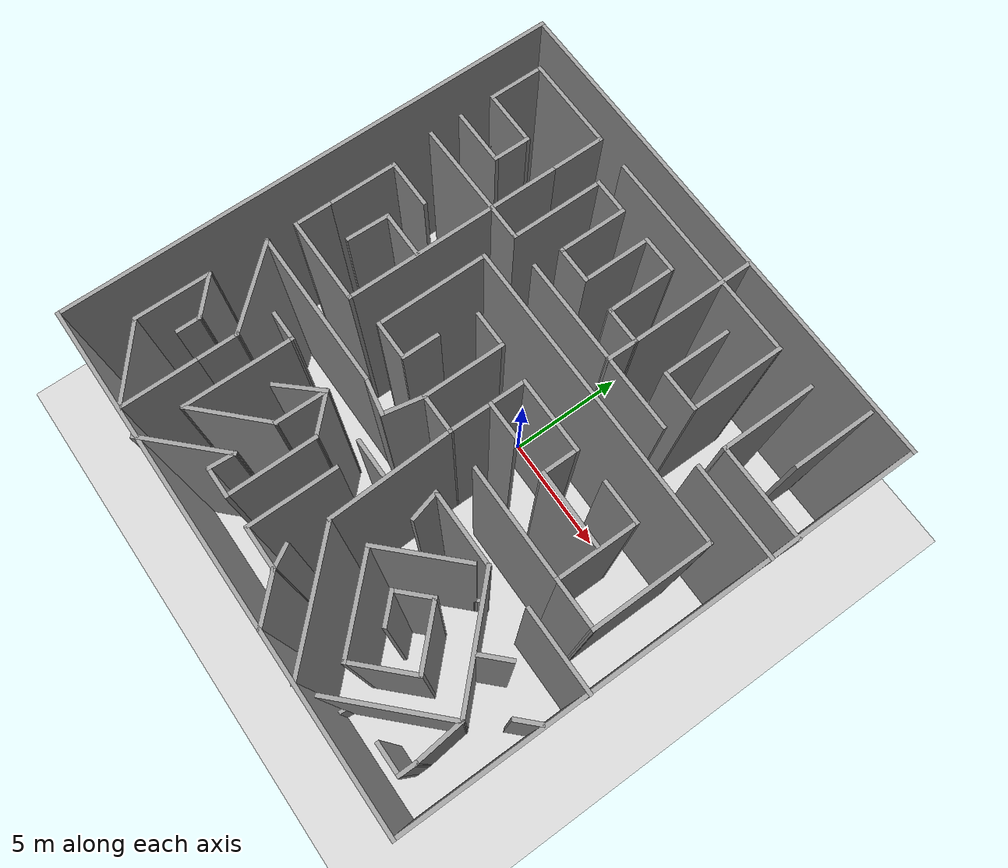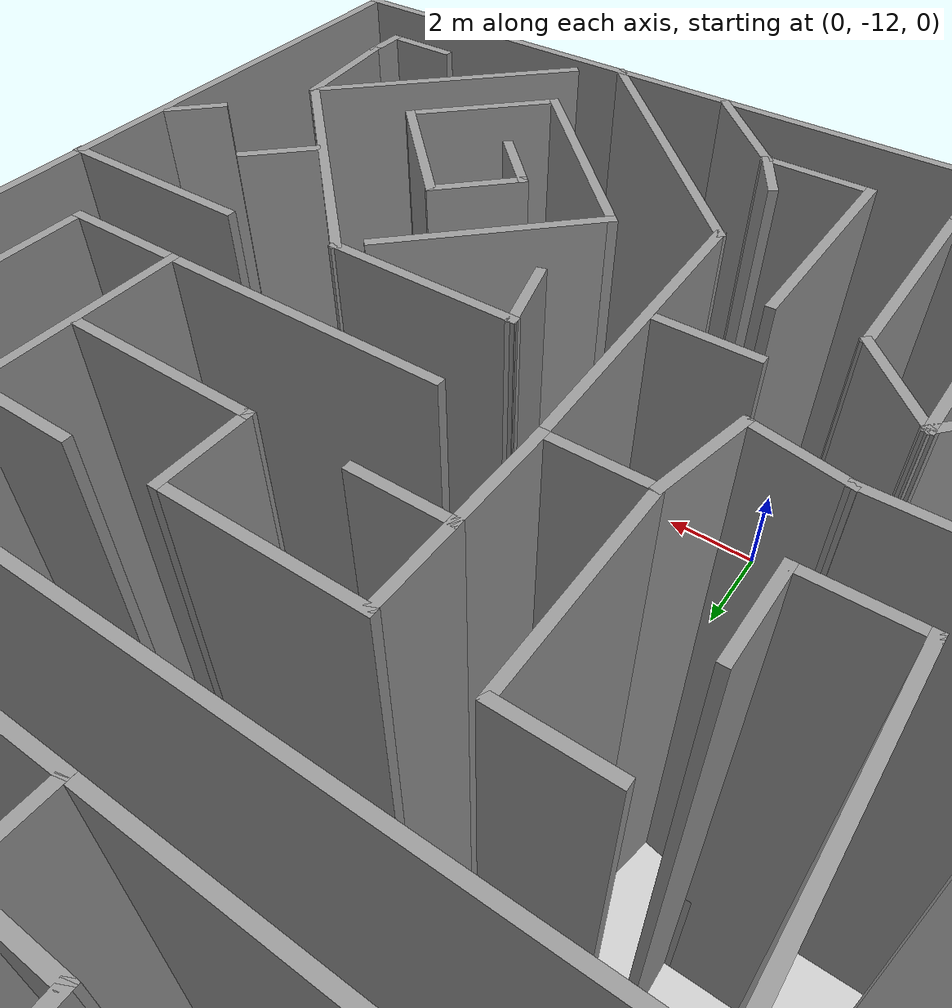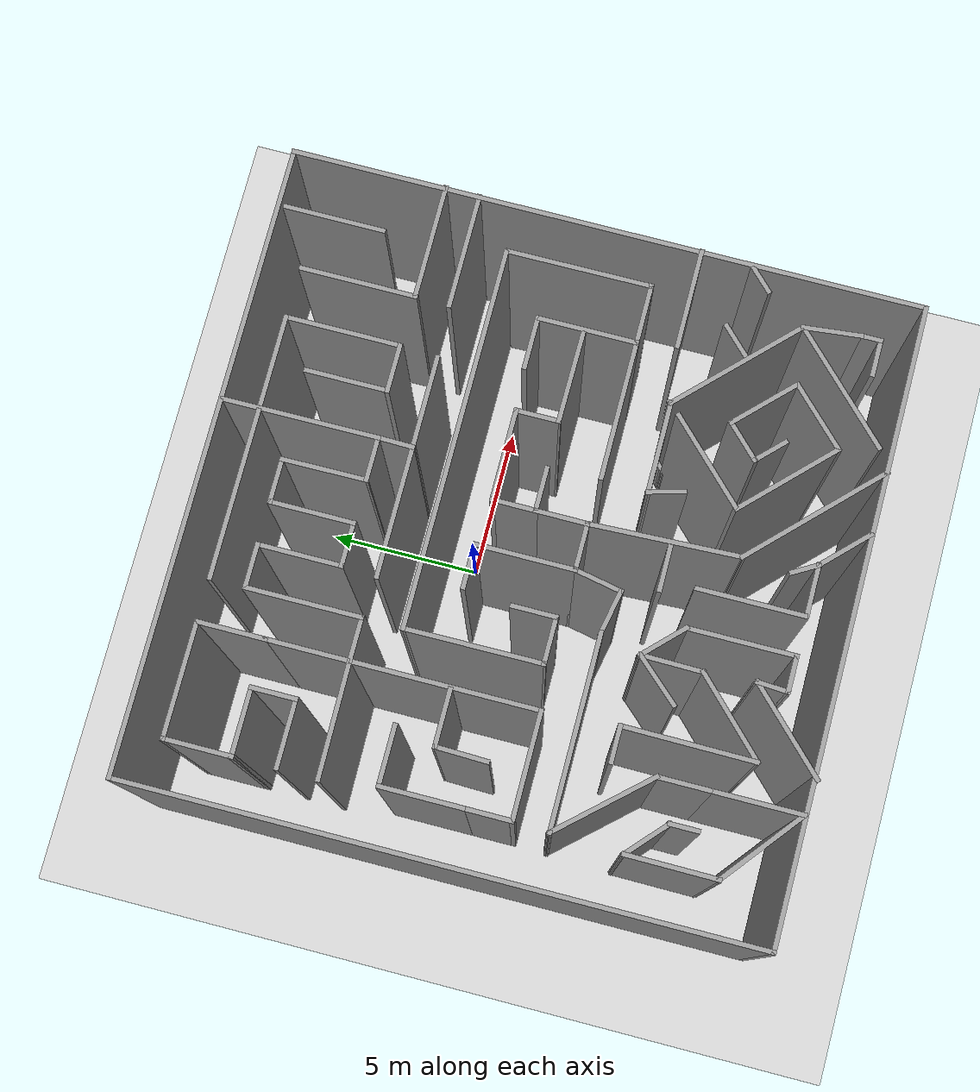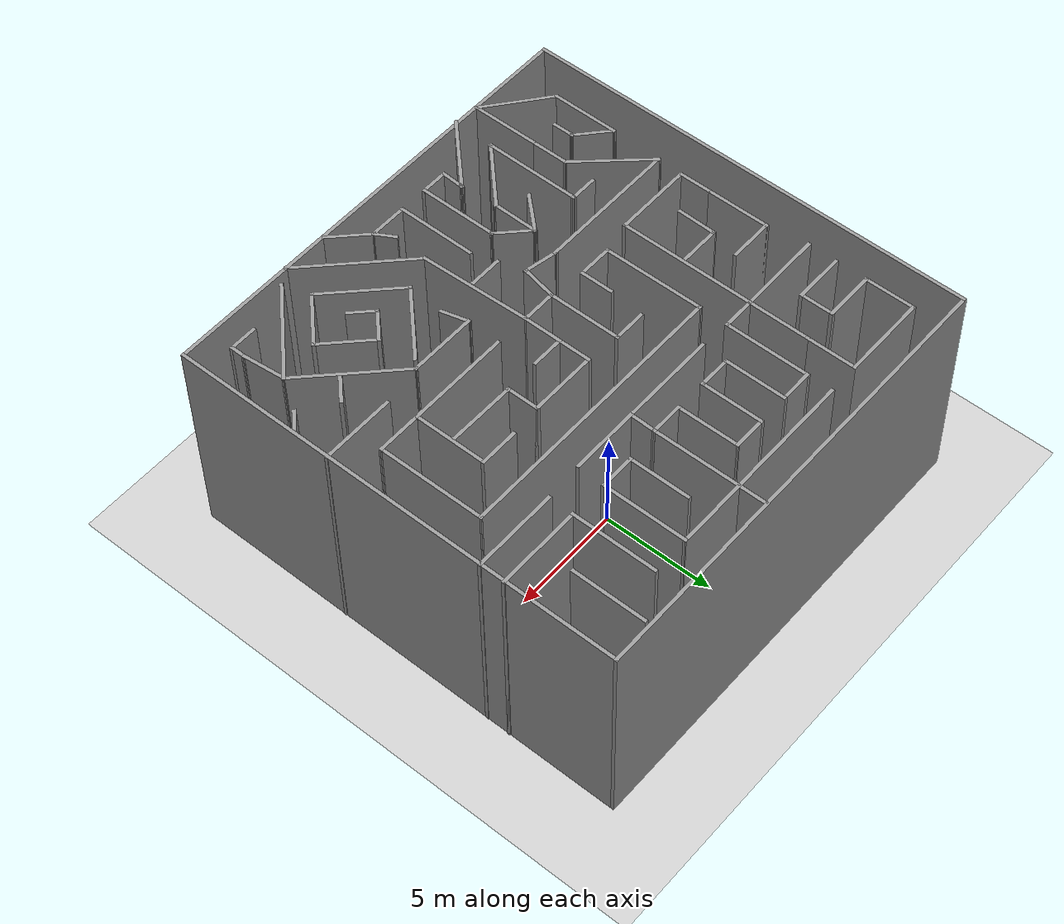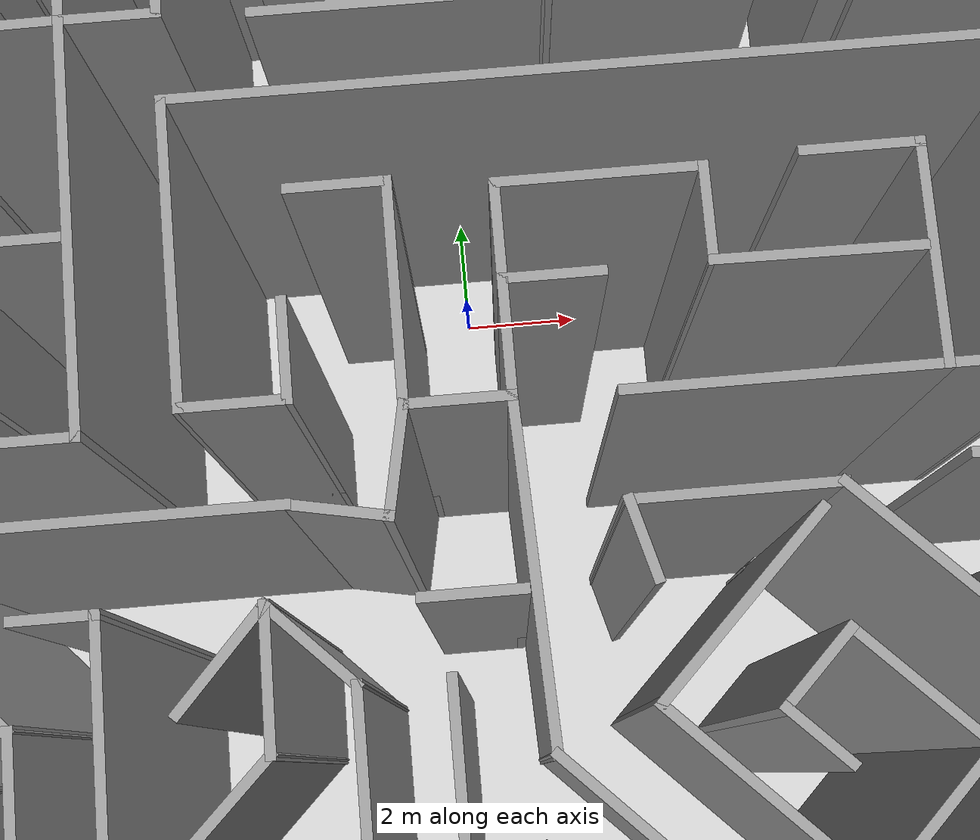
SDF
<sdf version="1.6">
 <world name="default">
  <include><uri>model://sun</uri></include>
  <scene><shadows>0</shadows></scene>
  <model name="ground_plane">
   <static>1</static>
   <link name="link">
    <collision name="collision">
     <geometry><plane><normal>0 0 1</normal><size>100 100</size></plane></geometry>
     <surface>
      <contact><collide_bitmask>65535</collide_bitmask></contact>
      <friction><ode><mu>100</mu><mu2>50</mu2></ode></friction>
     </surface>
    </collision>
    <visual name="visual">
     <cast_shadows>0</cast_shadows>
     <geometry><plane><normal>0 0 1</normal><size>100 100</size></plane></geometry>
     <material>
      <script><uri>file://media/materials/scripts/gazebo.material</uri><name>Gazebo/Grey</name></script>
     </material>
    </visual>
   </link>
  </model>
  <gravity>0 0 -9.8</gravity>
  <magnetic_field>6e-06 2.3e-05 -4.2e-05</magnetic_field>
  <atmosphere type="adiabatic"/>
  <plugin filename="librotors_gazebo_ros_interface_plugin.so" name="ros_interface_plugin"/>
  <physics default="0" name="default_physics" type="ode">
   <max_step_size>0.005</max_step_size>
   <real_time_factor>1</real_time_factor>
   <real_time_update_rate>600</real_time_update_rate>
   <gravity>0 0 -9.8</gravity>
   <magnetic_field>6e-06 2.3e-05 -4.2e-05</magnetic_field>
   <ode>
    <solver>
     <type>quick</type>
     <iters>1000</iters>
     <sor>1.3</sor>
     <use_dynamic_moi_rescaling>0</use_dynamic_moi_rescaling>
    </solver>
    <constraints>
     <cfm>0</cfm>
     <erp>0.2</erp>
     <contact_max_correcting_vel>100</contact_max_correcting_vel>
     <contact_surface_layer>0.001</contact_surface_layer>
    </constraints>
   </ode>
  </physics>
  <audio><device>default</device></audio>
  <spherical_coordinates>
   <surface_model>EARTH_WGS84</surface_model>
   <latitude_deg>0</latitude_deg>
   <longitude_deg>0</longitude_deg>
   <elevation>0</elevation>
   <heading_deg>0</heading_deg>
  </spherical_coordinates>
  <model name="maze.world">
   <pose>-0.346394 -1.90508 0 0 -0 0</pose>
   <link name="Wall_0">
    <collision name="Wall_0_Collision">
     <geometry><box><size>20.15 0.15 10</size></box></geometry>
     <pose>0 0 5 0 -0 0</pose>
    </collision>
    <visual name="Wall_0_Visual">
     <pose>0 0 5 0 -0 0</pose>
     <geometry><box><size>20.15 0.15 10</size></box></geometry>
     <material>
      <script><uri>file://media/materials/scripts/gazebo.material</uri><name>Gazebo/Grey</name></script>
      <ambient>1 1 1 1</ambient>
     </material>
     <meta><layer>0</layer></meta>
    </visual>
    <pose>-0.0165 10.056 0 0 -0 0</pose>
   </link>
   <link name="Wall_100">
    <collision name="Wall_100_Collision">
     <geometry><box><size>6.25 0.15 10</size></box></geometry>
     <pose>0 0 5 0 -0 0</pose>
    </collision>
    <visual name="Wall_100_Visual">
     <pose>0 0 5 0 -0 0</pose>
     <geometry><box><size>6.25 0.15 10</size></box></geometry>
     <material>
      <script><uri>file://media/materials/scripts/gazebo.material</uri><name>Gazebo/Grey</name></script>
      <ambient>1 1 1 1</ambient>
     </material>
     <meta><layer>0</layer></meta>
    </visual>
    <pose>-5.2635 -2.82601 0 0 -0 0</pose>
   </link>
   <link name="Wall_101">
    <collision name="Wall_101_Collision">
     <geometry><box><size>1.52533 0.15 10</size></box></geometry>
     <pose>0 0 5 0 -0 0</pose>
    </collision>
    <visual name="Wall_101_Visual">
     <pose>0 0 5 0 -0 0</pose>
     <geometry><box><size>1.52533 0.15 10</size></box></geometry>
     <material>
      <script><uri>file://media/materials/scripts/gazebo.material</uri><name>Gazebo/Grey</name></script>
      <ambient>1 1 1 1</ambient>
     </material>
     <meta><layer>0</layer></meta>
    </visual>
    <pose>-1.5385 -2.95851 0 0 -0 -0.193832</pose>
   </link>
   <link name="Wall_102">
    <collision name="Wall_102_Collision">
     <geometry><box><size>1.64901 0.15 10</size></box></geometry>
     <pose>0 0 5 0 -0 0</pose>
    </collision>
    <visual name="Wall_102_Visual">
     <pose>0 0 5 0 -0 0</pose>
     <geometry><box><size>1.64901 0.15 10</size></box></geometry>
     <material>
      <script><uri>file://media/materials/scripts/gazebo.material</uri><name>Gazebo/Grey</name></script>
      <ambient>1 1 1 1</ambient>
     </material>
     <meta><layer>0</layer></meta>
    </visual>
    <pose>-0.7195 -2.35552 0 0 -0 1.37746</pose>
   </link>
   <link name="Wall_104">
    <collision name="Wall_104_Collision">
     <geometry><box><size>3.69217 0.15 10</size></box></geometry>
     <pose>0 0 5 0 -0 0</pose>
    </collision>
    <visual name="Wall_104_Visual">
     <pose>0 0 5 0 -0 0</pose>
     <geometry><box><size>3.69217 0.15 10</size></box></geometry>
     <material>
      <script><uri>file://media/materials/scripts/gazebo.material</uri><name>Gazebo/Grey</name></script>
      <ambient>1 1 1 1</ambient>
     </material>
     <meta><layer>0</layer></meta>
    </visual>
    <pose>-7.1295 -4.14302 0 0 -0 -0.838527</pose>
   </link>
   <link name="Wall_105">
    <collision name="Wall_105_Collision">
     <geometry><box><size>1.75 0.15 10</size></box></geometry>
     <pose>0 0 5 0 -0 0</pose>
    </collision>
    <visual name="Wall_105_Visual">
     <pose>0 0 5 0 -0 0</pose>
     <geometry><box><size>1.75 0.15 10</size></box></geometry>
     <material>
      <script><uri>file://media/materials/scripts/gazebo.material</uri><name>Gazebo/Grey</name></script>
      <ambient>1 1 1 1</ambient>
     </material>
     <meta><layer>0</layer></meta>
    </visual>
    <pose>-5.9455 -6.26002 0 0 -0 -1.5708</pose>
   </link>
   <link name="Wall_106">
    <collision name="Wall_106_Collision">
     <geometry><box><size>3 0.15 10</size></box></geometry>
     <pose>0 0 5 0 -0 0</pose>
    </collision>
    <visual name="Wall_106_Visual">
     <pose>0 0 5 0 -0 0</pose>
     <geometry><box><size>3 0.15 10</size></box></geometry>
     <material>
      <script><uri>file://media/materials/scripts/gazebo.material</uri><name>Gazebo/Grey</name></script>
      <ambient>1 1 1 1</ambient>
     </material>
     <meta><layer>0</layer></meta>
    </visual>
    <pose>-5.9455 -8.48502 0 0 -0 -1.5708</pose>
   </link>
   <link name="Wall_11">
    <collision name="Wall_11_Collision">
     <geometry><box><size>2.25 0.15 10</size></box></geometry>
     <pose>0 0 5 0 -0 0</pose>
    </collision>
    <visual name="Wall_11_Visual">
     <pose>0 0 5 0 -0 0</pose>
     <geometry><box><size>2.25 0.15 10</size></box></geometry>
     <material>
      <script><uri>file://media/materials/scripts/gazebo.material</uri><name>Gazebo/Grey</name></script>
      <ambient>1 1 1 1</ambient>
     </material>
     <meta><layer>0</layer></meta>
    </visual>
    <pose>-8.5155 7.80598 0 0 -0 -1.5708</pose>
   </link>
   <link name="Wall_110">
    <collision name="Wall_110_Collision">
     <geometry><box><size>1.76243 0.15 10</size></box></geometry>
     <pose>0 0 5 0 -0 0</pose>
    </collision>
    <visual name="Wall_110_Visual">
     <pose>0 0 5 0 -0 0</pose>
     <geometry><box><size>1.76243 0.15 10</size></box></geometry>
     <material>
      <script><uri>file://media/materials/scripts/gazebo.material</uri><name>Gazebo/Grey</name></script>
      <ambient>1 1 1 1</ambient>
     </material>
     <meta><layer>0</layer></meta>
    </visual>
    <pose>-7.7785 -5.61402 0 0 -0 -0.7389</pose>
   </link>
   <link name="Wall_112">
    <collision name="Wall_112_Collision">
     <geometry><box><size>3.01561 0.15 10</size></box></geometry>
     <pose>0 0 5 0 -0 0</pose>
    </collision>
    <visual name="Wall_112_Visual">
     <pose>0 0 5 0 -0 0</pose>
     <geometry><box><size>3.01561 0.15 10</size></box></geometry>
     <material>
      <script><uri>file://media/materials/scripts/gazebo.material</uri><name>Gazebo/Grey</name></script>
      <ambient>1 1 1 1</ambient>
     </material>
     <meta><layer>0</layer></meta>
    </visual>
    <pose>-8.382 -6.50401 0 0 -0 -1.57603</pose>
   </link>
   <link name="Wall_113">
    <collision name="Wall_113_Collision">
     <geometry><box><size>3.29125 0.15 10</size></box></geometry>
     <pose>0 0 5 0 -0 0</pose>
    </collision>
    <visual name="Wall_113_Visual">
     <pose>0 0 5 0 -0 0</pose>
     <geometry><box><size>3.29125 0.15 10</size></box></geometry>
     <material>
      <script><uri>file://media/materials/scripts/gazebo.material</uri><name>Gazebo/Grey</name></script>
      <ambient>1 1 1 1</ambient>
     </material>
     <meta><layer>0</layer></meta>
    </visual>
    <pose>-7.1675 -8.92352 0 0 -0 -0.679166</pose>
   </link>
   <link name="Wall_115">
    <collision name="Wall_115_Collision">
     <geometry><box><size>1 0.15 10</size></box></geometry>
     <pose>0 0 5 0 -0 0</pose>
    </collision>
    <visual name="Wall_115_Visual">
     <pose>0 0 5 0 -0 0</pose>
     <geometry><box><size>1 0.15 10</size></box></geometry>
     <material>
      <script><uri>file://media/materials/scripts/gazebo.material</uri><name>Gazebo/Grey</name></script>
      <ambient>1 1 1 1</ambient>
     </material>
     <meta><layer>0</layer></meta>
    </visual>
    <pose>-7.1825 -6.58202 0 0 -0 -1.5708</pose>
   </link>
   <link name="Wall_117">
    <collision name="Wall_117_Collision">
     <geometry><box><size>1.25 0.15 10</size></box></geometry>
     <pose>0 0 5 0 -0 0</pose>
    </collision>
    <visual name="Wall_117_Visual">
     <pose>0 0 5 0 -0 0</pose>
     <geometry><box><size>1.25 0.15 10</size></box></geometry>
     <material>
      <script><uri>file://media/materials/scripts/gazebo.material</uri><name>Gazebo/Grey</name></script>
      <ambient>1 1 1 1</ambient>
     </material>
     <meta><layer>0</layer></meta>
    </visual>
    <pose>-5.3135 -4.05701 0 0 -0 0</pose>
   </link>
   <link name="Wall_118">
    <collision name="Wall_118_Collision">
     <geometry><box><size>4.30043 0.15 10</size></box></geometry>
     <pose>0 0 5 0 -0 0</pose>
    </collision>
    <visual name="Wall_118_Visual">
     <pose>0 0 5 0 -0 0</pose>
     <geometry><box><size>4.30043 0.15 10</size></box></geometry>
     <material>
      <script><uri>file://media/materials/scripts/gazebo.material</uri><name>Gazebo/Grey</name></script>
      <ambient>1 1 1 1</ambient>
     </material>
     <meta><layer>0</layer></meta>
    </visual>
    <pose>-4.777 -6.13202 0 0 -0 -1.5773</pose>
   </link>
   <link name="Wall_119">
    <collision name="Wall_119_Collision">
     <geometry><box><size>3.23166 0.15 10</size></box></geometry>
     <pose>0 0 5 0 -0 0</pose>
    </collision>
    <visual name="Wall_119_Visual">
     <pose>0 0 5 0 -0 0</pose>
     <geometry><box><size>3.23166 0.15 10</size></box></geometry>
     <material>
      <script><uri>file://media/materials/scripts/gazebo.material</uri><name>Gazebo/Grey</name></script>
      <ambient>1 1 1 1</ambient>
     </material>
     <meta><layer>0</layer></meta>
    </visual>
    <pose>-3.694 -7.12401 0 0 -0 0.779204</pose>
   </link>
   <link name="Wall_12">
    <collision name="Wall_12_Collision">
     <geometry><box><size>2.26035 0.15 10</size></box></geometry>
     <pose>0 0 5 0 -0 0</pose>
    </collision>
    <visual name="Wall_12_Visual">
     <pose>0 0 5 0 -0 0</pose>
     <geometry><box><size>2.26035 0.15 10</size></box></geometry>
     <material>
      <script><uri>file://media/materials/scripts/gazebo.material</uri><name>Gazebo/Grey</name></script>
      <ambient>1 1 1 1</ambient>
     </material>
     <meta><layer>0</layer></meta>
    </visual>
    <pose>-7.4605 6.75598 0 0 -0 0</pose>
   </link>
   <link name="Wall_120">
    <collision name="Wall_120_Collision">
     <geometry><box><size>2.0765 0.15 10</size></box></geometry>
     <pose>0 0 5 0 -0 0</pose>
    </collision>
    <visual name="Wall_120_Visual">
     <pose>0 0 5 0 -0 0</pose>
     <geometry><box><size>2.0765 0.15 10</size></box></geometry>
     <material>
      <script><uri>file://media/materials/scripts/gazebo.material</uri><name>Gazebo/Grey</name></script>
      <ambient>1 1 1 1</ambient>
     </material>
     <meta><layer>0</layer></meta>
    </visual>
    <pose>-2.5845 -5.07801 0 0 -0 1.5573</pose>
   </link>
   <link name="Wall_121">
    <collision name="Wall_121_Collision">
     <geometry><box><size>1.75 0.15 10</size></box></geometry>
     <pose>0 0 5 0 -0 0</pose>
    </collision>
    <visual name="Wall_121_Visual">
     <pose>0 0 5 0 -0 0</pose>
     <geometry><box><size>1.75 0.15 10</size></box></geometry>
     <material>
      <script><uri>file://media/materials/scripts/gazebo.material</uri><name>Gazebo/Grey</name></script>
      <ambient>1 1 1 1</ambient>
     </material>
     <meta><layer>0</layer></meta>
    </visual>
    <pose>-2.006 -4.68051 0 0 -0 -0.785398</pose>
   </link>
   <link name="Wall_122">
    <collision name="Wall_122_Collision">
     <geometry><box><size>3.5 0.15 10</size></box></geometry>
     <pose>0 0 5 0 -0 0</pose>
    </collision>
    <visual name="Wall_122_Visual">
     <pose>0 0 5 0 -0 0</pose>
     <geometry><box><size>3.5 0.15 10</size></box></geometry>
     <material>
      <script><uri>file://media/materials/scripts/gazebo.material</uri><name>Gazebo/Grey</name></script>
      <ambient>1 1 1 1</ambient>
     </material>
     <meta><layer>0</layer></meta>
    </visual>
    <pose>-1.4405 -6.92102 0 0 -0 -1.5708</pose>
   </link>
   <link name="Wall_123">
    <collision name="Wall_123_Collision">
     <geometry><box><size>1.25 0.15 10</size></box></geometry>
     <pose>0 0 5 0 -0 0</pose>
    </collision>
    <visual name="Wall_123_Visual">
     <pose>0 0 5 0 -0 0</pose>
     <geometry><box><size>1.25 0.15 10</size></box></geometry>
     <material>
      <script><uri>file://media/materials/scripts/gazebo.material</uri><name>Gazebo/Grey</name></script>
      <ambient>1 1 1 1</ambient>
     </material>
     <meta><layer>0</layer></meta>
    </visual>
    <pose>-1.9905 -8.59602 0 0 -0 3.14159</pose>
   </link>
   <link name="Wall_124">
    <collision name="Wall_124_Collision">
     <geometry><box><size>1.09165 0.15 10</size></box></geometry>
     <pose>0 0 5 0 -0 0</pose>
    </collision>
    <visual name="Wall_124_Visual">
     <pose>0 0 5 0 -0 0</pose>
     <geometry><box><size>1.09165 0.15 10</size></box></geometry>
     <material>
      <script><uri>file://media/materials/scripts/gazebo.material</uri><name>Gazebo/Grey</name></script>
      <ambient>1 1 1 1</ambient>
     </material>
     <meta><layer>0</layer></meta>
    </visual>
    <pose>-2.5115 -8.12602 0 0 -0 1.50917</pose>
   </link>
   <link name="Wall_126">
    <collision name="Wall_126_Collision">
     <geometry><box><size>1.9337 0.15 10</size></box></geometry>
     <pose>0 0 5 0 -0 0</pose>
    </collision>
    <visual name="Wall_126_Visual">
     <pose>0 0 5 0 -0 0</pose>
     <geometry><box><size>1.9337 0.15 10</size></box></geometry>
     <material>
      <script><uri>file://media/materials/scripts/gazebo.material</uri><name>Gazebo/Grey</name></script>
      <ambient>1 1 1 1</ambient>
     </material>
     <meta><layer>0</layer></meta>
    </visual>
    <pose>-3.173 -4.77352 0 0 -0 0.830605</pose>
   </link>
   <link name="Wall_128">
    <collision name="Wall_128_Collision">
     <geometry><box><size>3.5 0.15 10</size></box></geometry>
     <pose>0 0 5 0 -0 0</pose>
    </collision>
    <visual name="Wall_128_Visual">
     <pose>0 0 5 0 -0 0</pose>
     <geometry><box><size>3.5 0.15 10</size></box></geometry>
     <material>
      <script><uri>file://media/materials/scripts/gazebo.material</uri><name>Gazebo/Grey</name></script>
      <ambient>1 1 1 1</ambient>
     </material>
     <meta><layer>0</layer></meta>
    </visual>
    <pose>-3.667 -8.84051 0 0 -0 -2.35619</pose>
   </link>
   <link name="Wall_13">
    <collision name="Wall_13_Collision">
     <geometry><box><size>1.51899 0.15 10</size></box></geometry>
     <pose>0 0 5 0 -0 0</pose>
    </collision>
    <visual name="Wall_13_Visual">
     <pose>0 0 5 0 -0 0</pose>
     <geometry><box><size>1.51899 0.15 10</size></box></geometry>
     <material>
      <script><uri>file://media/materials/scripts/gazebo.material</uri><name>Gazebo/Grey</name></script>
      <ambient>1 1 1 1</ambient>
     </material>
     <meta><layer>0</layer></meta>
    </visual>
    <pose>-6.4055 6.07149 0 0 -0 -1.5708</pose>
   </link>
   <link name="Wall_130">
    <collision name="Wall_130_Collision">
     <geometry><box><size>1.25 0.15 10</size></box></geometry>
     <pose>0 0 5 0 -0 0</pose>
    </collision>
    <visual name="Wall_130_Visual">
     <pose>0 0 5 0 -0 0</pose>
     <geometry><box><size>1.25 0.15 10</size></box></geometry>
     <material>
      <script><uri>file://media/materials/scripts/gazebo.material</uri><name>Gazebo/Grey</name></script>
      <ambient>1 1 1 1</ambient>
     </material>
     <meta><layer>0</layer></meta>
    </visual>
    <pose>4.4255 -6.39102 0 0 -0 2.35619</pose>
   </link>
   <link name="Wall_131">
    <collision name="Wall_131_Collision">
     <geometry><box><size>1.5 0.15 10</size></box></geometry>
     <pose>0 0 5 0 -0 0</pose>
    </collision>
    <visual name="Wall_131_Visual">
     <pose>0 0 5 0 -0 0</pose>
     <geometry><box><size>1.5 0.15 10</size></box></geometry>
     <material>
      <script><uri>file://media/materials/scripts/gazebo.material</uri><name>Gazebo/Grey</name></script>
      <ambient>1 1 1 1</ambient>
     </material>
     <meta><layer>0</layer></meta>
    </visual>
    <pose>4.514 -5.52501 0 0 -0 0.784874</pose>
   </link>
   <link name="Wall_132">
    <collision name="Wall_132_Collision">
     <geometry><box><size>2.5 0.15 10</size></box></geometry>
     <pose>0 0 5 0 -0 0</pose>
    </collision>
    <visual name="Wall_132_Visual">
     <pose>0 0 5 0 -0 0</pose>
     <geometry><box><size>2.5 0.15 10</size></box></geometry>
     <material>
      <script><uri>file://media/materials/scripts/gazebo.material</uri><name>Gazebo/Grey</name></script>
      <ambient>1 1 1 1</ambient>
     </material>
     <meta><layer>0</layer></meta>
    </visual>
    <pose>5.8225 -5.87901 0 0 -0 -0.785398</pose>
   </link>
   <link name="Wall_133">
    <collision name="Wall_133_Collision">
     <geometry><box><size>2.5 0.15 10</size></box></geometry>
     <pose>0 0 5 0 -0 0</pose>
    </collision>
    <visual name="Wall_133_Visual">
     <pose>0 0 5 0 -0 0</pose>
     <geometry><box><size>2.5 0.15 10</size></box></geometry>
     <material>
      <script><uri>file://media/materials/scripts/gazebo.material</uri><name>Gazebo/Grey</name></script>
      <ambient>1 1 1 1</ambient>
     </material>
     <meta><layer>0</layer></meta>
    </visual>
    <pose>5.8225 -7.54052 0 0 -0 -2.35649</pose>
   </link>
   <link name="Wall_134">
    <collision name="Wall_134_Collision">
     <geometry><box><size>3.75 0.15 10</size></box></geometry>
     <pose>0 0 5 0 -0 0</pose>
    </collision>
    <visual name="Wall_134_Visual">
     <pose>0 0 5 0 -0 0</pose>
     <geometry><box><size>3.75 0.15 10</size></box></geometry>
     <material>
      <script><uri>file://media/materials/scripts/gazebo.material</uri><name>Gazebo/Grey</name></script>
      <ambient>1 1 1 1</ambient>
     </material>
     <meta><layer>0</layer></meta>
    </visual>
    <pose>3.7185 -7.09852 0 0 -0 2.35639</pose>
   </link>
   <link name="Wall_135">
    <collision name="Wall_135_Collision">
     <geometry><box><size>3.5 0.15 10</size></box></geometry>
     <pose>0 0 5 0 -0 0</pose>
    </collision>
    <visual name="Wall_135_Visual">
     <pose>0 0 5 0 -0 0</pose>
     <geometry><box><size>3.5 0.15 10</size></box></geometry>
     <material>
      <script><uri>file://media/materials/scripts/gazebo.material</uri><name>Gazebo/Grey</name></script>
      <ambient>1 1 1 1</ambient>
     </material>
     <meta><layer>0</layer></meta>
    </visual>
    <pose>3.63 -4.64152 0 0 -0 0.785398</pose>
   </link>
   <link name="Wall_136">
    <collision name="Wall_136_Collision">
     <geometry><box><size>0.15 0.15 2.5</size></box></geometry>
     <pose>0 0 1.25 0 -0 0</pose>
    </collision>
    <visual name="Wall_136_Visual">
     <pose>0 0 1.25 0 -0 0</pose>
     <geometry><box><size>0.15 0.15 2.5</size></box></geometry>
     <material>
      <script><uri>file://media/materials/scripts/gazebo.material</uri><name>Gazebo/Grey</name></script>
      <ambient>1 1 1 1</ambient>
     </material>
     <meta><layer>0</layer></meta>
    </visual>
    <pose>4.8145 -3.45702 0 0 -0 0</pose>
   </link>
   <link name="Wall_137">
    <collision name="Wall_137_Collision">
     <geometry><box><size>0.15 0.15 2.5</size></box></geometry>
     <pose>0 0 1.25 0 -0 0</pose>
    </collision>
    <visual name="Wall_137_Visual">
     <pose>0 0 1.25 0 -0 0</pose>
     <geometry><box><size>0.15 0.15 2.5</size></box></geometry>
     <material>
      <script><uri>file://media/materials/scripts/gazebo.material</uri><name>Gazebo/Grey</name></script>
      <ambient>1 1 1 1</ambient>
     </material>
     <meta><layer>0</layer></meta>
    </visual>
    <pose>4.8145 -3.45702 0 0 -0 0</pose>
   </link>
   <link name="Wall_138">
    <collision name="Wall_138_Collision">
     <geometry><box><size>0.25 0.15 2.5</size></box></geometry>
     <pose>0 0 1.25 0 -0 0</pose>
    </collision>
    <visual name="Wall_138_Visual">
     <pose>0 0 1.25 0 -0 0</pose>
     <geometry><box><size>0.25 0.15 2.5</size></box></geometry>
     <material>
      <script><uri>file://media/materials/scripts/gazebo.material</uri><name>Gazebo/Grey</name></script>
      <ambient>1 1 1 1</ambient>
     </material>
     <meta><layer>0</layer></meta>
    </visual>
    <pose>4.85001 -3.42161 0 0 -0 0.784014</pose>
   </link>
   <link name="Wall_139">
    <collision name="Wall_139_Collision">
     <geometry><box><size>0.5 0.15 2.5</size></box></geometry>
     <pose>0 0 1.25 0 -0 0</pose>
    </collision>
    <visual name="Wall_139_Visual">
     <pose>0 0 1.25 0 -0 0</pose>
     <geometry><box><size>0.5 0.15 2.5</size></box></geometry>
     <material>
      <script><uri>file://media/materials/scripts/gazebo.material</uri><name>Gazebo/Grey</name></script>
      <ambient>1 1 1 1</ambient>
     </material>
     <meta><layer>0</layer></meta>
    </visual>
    <pose>5.00951 -3.26261 0 0 -0 0.783775</pose>
   </link>
   <link name="Wall_14">
    <collision name="Wall_14_Collision">
     <geometry><box><size>2.25 0.15 10</size></box></geometry>
     <pose>0 0 5 0 -0 0</pose>
    </collision>
    <visual name="Wall_14_Visual">
     <pose>0 0 5 0 -0 0</pose>
     <geometry><box><size>2.25 0.15 10</size></box></geometry>
     <material>
      <script><uri>file://media/materials/scripts/gazebo.material</uri><name>Gazebo/Grey</name></script>
      <ambient>1 1 1 1</ambient>
     </material>
     <meta><layer>0</layer></meta>
    </visual>
    <pose>-7.4555 5.38698 0 0 -0 3.14159</pose>
   </link>
   <link name="Wall_140">
    <collision name="Wall_140_Collision">
     <geometry><box><size>4.75 0.15 10</size></box></geometry>
     <pose>0 0 5 0 -0 0</pose>
    </collision>
    <visual name="Wall_140_Visual">
     <pose>0 0 5 0 -0 0</pose>
     <geometry><box><size>4.75 0.15 10</size></box></geometry>
     <material>
      <script><uri>file://media/materials/scripts/gazebo.material</uri><name>Gazebo/Grey</name></script>
      <ambient>1 1 1 1</ambient>
     </material>
     <meta><layer>0</layer></meta>
    </visual>
    <pose>6.7595 -4.76502 0 0 -0 -0.785398</pose>
   </link>
   <link name="Wall_141">
    <collision name="Wall_141_Collision">
     <geometry><box><size>0.248595 0.15 2.5</size></box></geometry>
     <pose>0 0 1.25 0 -0 0</pose>
    </collision>
    <visual name="Wall_141_Visual">
     <pose>0 0 1.25 0 -0 0</pose>
     <geometry><box><size>0.248595 0.15 2.5</size></box></geometry>
     <material>
      <script><uri>file://media/materials/scripts/gazebo.material</uri><name>Gazebo/Grey</name></script>
      <ambient>1 1 1 1</ambient>
     </material>
     <meta><layer>0</layer></meta>
    </visual>
    <pose>8.4175 -6.42851 0 0 -0 -0.86437</pose>
   </link>
   <link name="Wall_142">
    <collision name="Wall_142_Collision">
     <geometry><box><size>4.51417 0.15 10</size></box></geometry>
     <pose>0 0 5 0 -0 0</pose>
    </collision>
    <visual name="Wall_142_Visual">
     <pose>0 0 5 0 -0 0</pose>
     <geometry><box><size>4.51417 0.15 10</size></box></geometry>
     <material>
      <script><uri>file://media/materials/scripts/gazebo.material</uri><name>Gazebo/Grey</name></script>
      <ambient>1 1 1 1</ambient>
     </material>
     <meta><layer>0</layer></meta>
    </visual>
    <pose>6.9015 -8.00402 0 0 -0 -2.35943</pose>
   </link>
   <link name="Wall_143">
    <collision name="Wall_143_Collision">
     <geometry><box><size>0.573691 0.15 2.5</size></box></geometry>
     <pose>0 0 1.25 0 -0 0</pose>
    </collision>
    <visual name="Wall_143_Visual">
     <pose>0 0 1.25 0 -0 0</pose>
     <geometry><box><size>0.573691 0.15 2.5</size></box></geometry>
     <material>
      <script><uri>file://media/materials/scripts/gazebo.material</uri><name>Gazebo/Grey</name></script>
      <ambient>1 1 1 1</ambient>
     </material>
     <meta><layer>0</layer></meta>
    </visual>
    <pose>5.32664 -9.75215 0 0 -0 -1.69792</pose>
   </link>
   <link name="Wall_147">
    <collision name="Wall_147_Collision">
     <geometry><box><size>5.25 0.15 10</size></box></geometry>
     <pose>0 0 5 0 -0 0</pose>
    </collision>
    <visual name="Wall_147_Visual">
     <pose>0 0 5 0 -0 0</pose>
     <geometry><box><size>5.25 0.15 10</size></box></geometry>
     <material>
      <script><uri>file://media/materials/scripts/gazebo.material</uri><name>Gazebo/Grey</name></script>
      <ambient>1 1 1 1</ambient>
     </material>
     <meta><layer>0</layer></meta>
    </visual>
    <pose>2.8625 -8.14602 0 0 -0 -0.785398</pose>
   </link>
   <link name="Wall_149">
    <collision name="Wall_149_Collision">
     <geometry><box><size>4.87629 0.15 10</size></box></geometry>
     <pose>0 0 5 0 -0 0</pose>
    </collision>
    <visual name="Wall_149_Visual">
     <pose>0 0 5 0 -0 0</pose>
     <geometry><box><size>4.87629 0.15 10</size></box></geometry>
     <material>
      <script><uri>file://media/materials/scripts/gazebo.material</uri><name>Gazebo/Grey</name></script>
      <ambient>1 1 1 1</ambient>
     </material>
     <meta><layer>0</layer></meta>
    </visual>
    <pose>0.967 -3.98151 0 0 -0 1.60995</pose>
   </link>
   <link name="Wall_153">
    <collision name="Wall_153_Collision">
     <geometry><box><size>1.5 0.15 10</size></box></geometry>
     <pose>0 0 5 0 -0 0</pose>
    </collision>
    <visual name="Wall_153_Visual">
     <pose>0 0 5 0 -0 0</pose>
     <geometry><box><size>1.5 0.15 10</size></box></geometry>
     <material>
      <script><uri>file://media/materials/scripts/gazebo.material</uri><name>Gazebo/Grey</name></script>
      <ambient>1 1 1 1</ambient>
     </material>
     <meta><layer>0</layer></meta>
    </visual>
    <pose>0.1455 -4.19102 0 0 -0 0</pose>
   </link>
   <link name="Wall_154">
    <collision name="Wall_154_Collision">
     <geometry><box><size>0.15 0.15 2.5</size></box></geometry>
     <pose>0 0 1.25 0 -0 0</pose>
    </collision>
    <visual name="Wall_154_Visual">
     <pose>0 0 1.25 0 -0 0</pose>
     <geometry><box><size>0.15 0.15 2.5</size></box></geometry>
     <material>
      <script><uri>file://media/materials/scripts/gazebo.material</uri><name>Gazebo/Grey</name></script>
      <ambient>1 1 1 1</ambient>
     </material>
     <meta><layer>0</layer></meta>
    </visual>
    <pose>0.8205 -4.19102 0 0 -0 0</pose>
   </link>
   <link name="Wall_156">
    <collision name="Wall_156_Collision">
     <geometry><box><size>3.5 0.15 10</size></box></geometry>
     <pose>0 0 5 0 -0 0</pose>
    </collision>
    <visual name="Wall_156_Visual">
     <pose>0 0 5 0 -0 0</pose>
     <geometry><box><size>3.5 0.15 10</size></box></geometry>
     <material>
      <script><uri>file://media/materials/scripts/gazebo.material</uri><name>Gazebo/Grey</name></script>
      <ambient>1 1 1 1</ambient>
     </material>
     <meta><layer>0</layer></meta>
    </visual>
    <pose>-0.2085 -6.93201 0 0 -0 -1.5708</pose>
   </link>
   <link name="Wall_157">
    <collision name="Wall_157_Collision">
     <geometry><box><size>1.75 0.15 10</size></box></geometry>
     <pose>0 0 5 0 -0 0</pose>
    </collision>
    <visual name="Wall_157_Visual">
     <pose>0 0 5 0 -0 0</pose>
     <geometry><box><size>1.75 0.15 10</size></box></geometry>
     <material>
      <script><uri>file://media/materials/scripts/gazebo.material</uri><name>Gazebo/Grey</name></script>
      <ambient>1 1 1 1</ambient>
     </material>
     <meta><layer>0</layer></meta>
    </visual>
    <pose>0.5915 -8.60702 0 0 -0 0</pose>
   </link>
   <link name="Wall_158">
    <collision name="Wall_158_Collision">
     <geometry><box><size>2 0.15 10</size></box></geometry>
     <pose>0 0 5 0 -0 0</pose>
    </collision>
    <visual name="Wall_158_Visual">
     <pose>0 0 5 0 -0 0</pose>
     <geometry><box><size>2 0.15 10</size></box></geometry>
     <material>
      <script><uri>file://media/materials/scripts/gazebo.material</uri><name>Gazebo/Grey</name></script>
      <ambient>1 1 1 1</ambient>
     </material>
     <meta><layer>0</layer></meta>
    </visual>
    <pose>2.046 -9.26102 0 0 -0 -0.785016</pose>
   </link>
   <link name="Wall_160">
    <collision name="Wall_160_Collision">
     <geometry><box><size>1 0.15 10</size></box></geometry>
     <pose>0 0 5 0 -0 0</pose>
    </collision>
    <visual name="Wall_160_Visual">
     <pose>0 0 5 0 -0 0</pose>
     <geometry><box><size>1 0.15 10</size></box></geometry>
     <material>
      <script><uri>file://media/materials/scripts/gazebo.material</uri><name>Gazebo/Grey</name></script>
      <ambient>1 1 1 1</ambient>
     </material>
     <meta><layer>0</layer></meta>
    </visual>
    <pose>1.179 -8.23902 0 0 -0 -1.04713</pose>
   </link>
   <link name="Wall_162">
    <collision name="Wall_162_Collision">
     <geometry><box><size>3.25 0.15 10</size></box></geometry>
     <pose>0 0 5 0 -0 0</pose>
    </collision>
    <visual name="Wall_162_Visual">
     <pose>0 0 5 0 -0 0</pose>
     <geometry><box><size>3.25 0.15 10</size></box></geometry>
     <material>
      <script><uri>file://media/materials/scripts/gazebo.material</uri><name>Gazebo/Grey</name></script>
      <ambient>1 1 1 1</ambient>
     </material>
     <meta><layer>0</layer></meta>
    </visual>
    <pose>8.4565 -2.90002 0 0 -0 0</pose>
   </link>
   <link name="Wall_165">
    <collision name="Wall_165_Collision">
     <geometry><box><size>3 0.15 10</size></box></geometry>
     <pose>0 0 5 0 -0 0</pose>
    </collision>
    <visual name="Wall_165_Visual">
     <pose>0 0 5 0 -0 0</pose>
     <geometry><box><size>3 0.15 10</size></box></geometry>
     <material>
      <script><uri>file://media/materials/scripts/gazebo.material</uri><name>Gazebo/Grey</name></script>
      <ambient>1 1 1 1</ambient>
     </material>
     <meta><layer>0</layer></meta>
    </visual>
    <pose>3.7085 -3.13902 0 0 -0 3.14159</pose>
   </link>
   <link name="Wall_166">
    <collision name="Wall_166_Collision">
     <geometry><box><size>1.25 0.15 10</size></box></geometry>
     <pose>0 0 5 0 -0 0</pose>
    </collision>
    <visual name="Wall_166_Visual">
     <pose>0 0 5 0 -0 0</pose>
     <geometry><box><size>1.25 0.15 10</size></box></geometry>
     <material>
      <script><uri>file://media/materials/scripts/gazebo.material</uri><name>Gazebo/Grey</name></script>
      <ambient>1 1 1 1</ambient>
     </material>
     <meta><layer>0</layer></meta>
    </visual>
    <pose>2.4255 -3.67002 0 0 -0 -1.30949</pose>
   </link>
   <link name="Wall_168">
    <collision name="Wall_168_Collision">
     <geometry><box><size>1.25 0.15 10</size></box></geometry>
     <pose>0 0 5 0 -0 0</pose>
    </collision>
    <visual name="Wall_168_Visual">
     <pose>0 0 5 0 -0 0</pose>
     <geometry><box><size>1.25 0.15 10</size></box></geometry>
     <material>
      <script><uri>file://media/materials/scripts/gazebo.material</uri><name>Gazebo/Grey</name></script>
      <ambient>1 1 1 1</ambient>
     </material>
     <meta><layer>0</layer></meta>
    </visual>
    <pose>7.5155 -4.58502 0 0 -0 0.785398</pose>
   </link>
   <link name="Wall_17">
    <collision name="Wall_17_Collision">
     <geometry><box><size>3.75 0.15 10</size></box></geometry>
     <pose>0 0 5 0 -0 0</pose>
    </collision>
    <visual name="Wall_17_Visual">
     <pose>0 0 5 0 -0 0</pose>
     <geometry><box><size>3.75 0.15 10</size></box></geometry>
     <material>
      <script><uri>file://media/materials/scripts/gazebo.material</uri><name>Gazebo/Grey</name></script>
      <ambient>1 1 1 1</ambient>
     </material>
     <meta><layer>0</layer></meta>
    </visual>
    <pose>-6.7155 8.85599 0 0 -0 0</pose>
   </link>
   <link name="Wall_170">
    <collision name="Wall_170_Collision">
     <geometry><box><size>1 0.15 10</size></box></geometry>
     <pose>0 0 5 0 -0 0</pose>
    </collision>
    <visual name="Wall_170_Visual">
     <pose>0 0 5 0 -0 0</pose>
     <geometry><box><size>1 0.15 10</size></box></geometry>
     <material>
      <script><uri>file://media/materials/scripts/gazebo.material</uri><name>Gazebo/Grey</name></script>
      <ambient>1 1 1 1</ambient>
     </material>
     <meta><layer>0</layer></meta>
    </visual>
    <pose>9.592 -4.87552 0 0 -0 -2.35619</pose>
   </link>
   <link name="Wall_172">
    <collision name="Wall_172_Collision">
     <geometry><box><size>1.93325 0.15 10</size></box></geometry>
     <pose>0 0 5 0 -0 0</pose>
    </collision>
    <visual name="Wall_172_Visual">
     <pose>0 0 5 0 -0 0</pose>
     <geometry><box><size>1.93325 0.15 10</size></box></geometry>
     <material>
      <script><uri>file://media/materials/scripts/gazebo.material</uri><name>Gazebo/Grey</name></script>
      <ambient>1 1 1 1</ambient>
     </material>
     <meta><layer>0</layer></meta>
    </visual>
    <pose>8.5415 -7.35252 0 0 -0 -1.46739</pose>
   </link>
   <link name="Wall_173">
    <collision name="Wall_173_Collision">
     <geometry><box><size>0.75 0.15 10</size></box></geometry>
     <pose>0 0 5 0 -0 0</pose>
    </collision>
    <visual name="Wall_173_Visual">
     <pose>0 0 5 0 -0 0</pose>
     <geometry><box><size>0.75 0.15 10</size></box></geometry>
     <material>
      <script><uri>file://media/materials/scripts/gazebo.material</uri><name>Gazebo/Grey</name></script>
      <ambient>1 1 1 1</ambient>
     </material>
     <meta><layer>0</layer></meta>
    </visual>
    <pose>8.6335 -8.53902 0 0 -0 -1.5708</pose>
   </link>
   <link name="Wall_176">
    <collision name="Wall_176_Collision">
     <geometry><box><size>1.25 0.15 10</size></box></geometry>
     <pose>0 0 5 0 -0 0</pose>
    </collision>
    <visual name="Wall_176_Visual">
     <pose>0 0 5 0 -0 0</pose>
     <geometry><box><size>1.25 0.15 10</size></box></geometry>
     <material>
      <script><uri>file://media/materials/scripts/gazebo.material</uri><name>Gazebo/Grey</name></script>
      <ambient>1 1 1 1</ambient>
     </material>
     <meta><layer>0</layer></meta>
    </visual>
    <pose>8.0835 -8.83902 0 0 -0 0</pose>
   </link>
   <link name="Wall_18">
    <collision name="Wall_18_Collision">
     <geometry><box><size>2.25 0.15 10</size></box></geometry>
     <pose>0 0 5 0 -0 0</pose>
    </collision>
    <visual name="Wall_18_Visual">
     <pose>0 0 5 0 -0 0</pose>
     <geometry><box><size>2.25 0.15 10</size></box></geometry>
     <material>
      <script><uri>file://media/materials/scripts/gazebo.material</uri><name>Gazebo/Grey</name></script>
      <ambient>1 1 1 1</ambient>
     </material>
     <meta><layer>0</layer></meta>
    </visual>
    <pose>-4.9155 7.80598 0 0 -0 -1.5708</pose>
   </link>
   <link name="Wall_19">
    <collision name="Wall_19_Collision">
     <geometry><box><size>2.75 0.15 10</size></box></geometry>
     <pose>0 0 5 0 -0 0</pose>
    </collision>
    <visual name="Wall_19_Visual">
     <pose>0 0 5 0 -0 0</pose>
     <geometry><box><size>2.75 0.15 10</size></box></geometry>
     <material>
      <script><uri>file://media/materials/scripts/gazebo.material</uri><name>Gazebo/Grey</name></script>
      <ambient>1 1 1 1</ambient>
     </material>
     <meta><layer>0</layer></meta>
    </visual>
    <pose>-4.9155 5.45599 0 0 -0 -1.5708</pose>
   </link>
   <link name="Wall_20">
    <collision name="Wall_20_Collision">
     <geometry><box><size>1.5 0.15 10</size></box></geometry>
     <pose>0 0 5 0 -0 0</pose>
    </collision>
    <visual name="Wall_20_Visual">
     <pose>0 0 5 0 -0 0</pose>
     <geometry><box><size>1.5 0.15 10</size></box></geometry>
     <material>
      <script><uri>file://media/materials/scripts/gazebo.material</uri><name>Gazebo/Grey</name></script>
      <ambient>1 1 1 1</ambient>
     </material>
     <meta><layer>0</layer></meta>
    </visual>
    <pose>-4.2405 4.15598 0 0 -0 0</pose>
   </link>
   <link name="Wall_21">
    <collision name="Wall_21_Collision">
     <geometry><box><size>3.75 0.15 10</size></box></geometry>
     <pose>0 0 5 0 -0 0</pose>
    </collision>
    <visual name="Wall_21_Visual">
     <pose>0 0 5 0 -0 0</pose>
     <geometry><box><size>3.75 0.15 10</size></box></geometry>
     <material>
      <script><uri>file://media/materials/scripts/gazebo.material</uri><name>Gazebo/Grey</name></script>
      <ambient>1 1 1 1</ambient>
     </material>
     <meta><layer>0</layer></meta>
    </visual>
    <pose>-3.5655 5.95599 0 0 -0 1.5708</pose>
   </link>
   <link name="Wall_22">
    <collision name="Wall_22_Collision">
     <geometry><box><size>1.5 0.15 10</size></box></geometry>
     <pose>0 0 5 0 -0 0</pose>
    </collision>
    <visual name="Wall_22_Visual">
     <pose>0 0 5 0 -0 0</pose>
     <geometry><box><size>1.5 0.15 10</size></box></geometry>
     <material>
      <script><uri>file://media/materials/scripts/gazebo.material</uri><name>Gazebo/Grey</name></script>
      <ambient>1 1 1 1</ambient>
     </material>
     <meta><layer>0</layer></meta>
    </visual>
    <pose>-2.8905 7.75598 0 0 -0 0</pose>
   </link>
   <link name="Wall_23">
    <collision name="Wall_23_Collision">
     <geometry><box><size>2.75 0.15 10</size></box></geometry>
     <pose>0 0 5 0 -0 0</pose>
    </collision>
    <visual name="Wall_23_Visual">
     <pose>0 0 5 0 -0 0</pose>
     <geometry><box><size>2.75 0.15 10</size></box></geometry>
     <material>
      <script><uri>file://media/materials/scripts/gazebo.material</uri><name>Gazebo/Grey</name></script>
      <ambient>1 1 1 1</ambient>
     </material>
     <meta><layer>0</layer></meta>
    </visual>
    <pose>-2.2155 6.45599 0 0 -0 -1.5708</pose>
   </link>
   <link name="Wall_24">
    <collision name="Wall_24_Collision">
     <geometry><box><size>1.5 0.15 10</size></box></geometry>
     <pose>0 0 5 0 -0 0</pose>
    </collision>
    <visual name="Wall_24_Visual">
     <pose>0 0 5 0 -0 0</pose>
     <geometry><box><size>1.5 0.15 10</size></box></geometry>
     <material>
      <script><uri>file://media/materials/scripts/gazebo.material</uri><name>Gazebo/Grey</name></script>
      <ambient>1 1 1 1</ambient>
     </material>
     <meta><layer>0</layer></meta>
    </visual>
    <pose>-1.5405 5.15598 0 0 -0 0</pose>
   </link>
   <link name="Wall_25">
    <collision name="Wall_25_Collision">
     <geometry><box><size>2.75 0.15 10</size></box></geometry>
     <pose>0 0 5 0 -0 0</pose>
    </collision>
    <visual name="Wall_25_Visual">
     <pose>0 0 5 0 -0 0</pose>
     <geometry><box><size>2.75 0.15 10</size></box></geometry>
     <material>
      <script><uri>file://media/materials/scripts/gazebo.material</uri><name>Gazebo/Grey</name></script>
      <ambient>1 1 1 1</ambient>
     </material>
     <meta><layer>0</layer></meta>
    </visual>
    <pose>-0.865499 6.45599 0 0 -0 1.5708</pose>
   </link>
   <link name="Wall_26">
    <collision name="Wall_26_Collision">
     <geometry><box><size>1.5 0.15 10</size></box></geometry>
     <pose>0 0 5 0 -0 0</pose>
    </collision>
    <visual name="Wall_26_Visual">
     <pose>0 0 5 0 -0 0</pose>
     <geometry><box><size>1.5 0.15 10</size></box></geometry>
     <material>
      <script><uri>file://media/materials/scripts/gazebo.material</uri><name>Gazebo/Grey</name></script>
      <ambient>1 1 1 1</ambient>
     </material>
     <meta><layer>0</layer></meta>
    </visual>
    <pose>-0.1905 7.75598 0 0 -0 0</pose>
   </link>
   <link name="Wall_27">
    <collision name="Wall_27_Collision">
     <geometry><box><size>2.76984 0.15 10</size></box></geometry>
     <pose>0 0 5 0 -0 0</pose>
    </collision>
    <visual name="Wall_27_Visual">
     <pose>0 0 5 0 -0 0</pose>
     <geometry><box><size>2.76984 0.15 10</size></box></geometry>
     <material>
      <script><uri>file://media/materials/scripts/gazebo.material</uri><name>Gazebo/Grey</name></script>
      <ambient>1 1 1 1</ambient>
     </material>
     <meta><layer>0</layer></meta>
    </visual>
    <pose>0.4945 6.44598 0 0 -0 -1.56316</pose>
   </link>
   <link name="Wall_28">
    <collision name="Wall_28_Collision">
     <geometry><box><size>1.5 0.15 10</size></box></geometry>
     <pose>0 0 5 0 -0 0</pose>
    </collision>
    <visual name="Wall_28_Visual">
     <pose>0 0 5 0 -0 0</pose>
     <geometry><box><size>1.5 0.15 10</size></box></geometry>
     <material>
      <script><uri>file://media/materials/scripts/gazebo.material</uri><name>Gazebo/Grey</name></script>
      <ambient>1 1 1 1</ambient>
     </material>
     <meta><layer>0</layer></meta>
    </visual>
    <pose>1.1795 5.13598 0 0 -0 0</pose>
   </link>
   <link name="Wall_29">
    <collision name="Wall_29_Collision">
     <geometry><box><size>5.01971 0.15 10</size></box></geometry>
     <pose>0 0 5 0 -0 0</pose>
    </collision>
    <visual name="Wall_29_Visual">
     <pose>0 0 5 0 -0 0</pose>
     <geometry><box><size>5.01971 0.15 10</size></box></geometry>
     <material>
      <script><uri>file://media/materials/scripts/gazebo.material</uri><name>Gazebo/Grey</name></script>
      <ambient>1 1 1 1</ambient>
     </material>
     <meta><layer>0</layer></meta>
    </visual>
    <pose>1.8445 7.57098 0 0 -0 1.5749</pose>
   </link>
   <link name="Wall_3">
    <collision name="Wall_3_Collision">
     <geometry><box><size>20.15 0.15 10</size></box></geometry>
     <pose>0 0 5 0 -0 0</pose>
    </collision>
    <visual name="Wall_3_Visual">
     <pose>0 0 5 0 -0 0</pose>
     <geometry><box><size>20.15 0.15 10</size></box></geometry>
     <material>
      <script><uri>file://media/materials/scripts/gazebo.material</uri><name>Gazebo/Grey</name></script>
      <ambient>1 1 1 1</ambient>
     </material>
     <meta><layer>0</layer></meta>
    </visual>
    <pose>-0.0165 -9.94402 0 0 -0 0</pose>
   </link>
   <link name="Wall_34">
    <collision name="Wall_34_Collision">
     <geometry><box><size>3.74753 0.15 10</size></box></geometry>
     <pose>0 0 5 0 -0 0</pose>
    </collision>
    <visual name="Wall_34_Visual">
     <pose>0 0 5 0 -0 0</pose>
     <geometry><box><size>3.74753 0.15 10</size></box></geometry>
     <material>
      <script><uri>file://media/materials/scripts/gazebo.material</uri><name>Gazebo/Grey</name></script>
      <ambient>1 1 1 1</ambient>
     </material>
     <meta><layer>0</layer></meta>
    </visual>
    <pose>4.8 7.05499 0 0 -0 -1.57107</pose>
   </link>
   <link name="Wall_36">
    <collision name="Wall_36_Collision">
     <geometry><box><size>8.5 0.15 10</size></box></geometry>
     <pose>0 0 5 0 -0 0</pose>
    </collision>
    <visual name="Wall_36_Visual">
     <pose>0 0 5 0 -0 0</pose>
     <geometry><box><size>8.5 0.15 10</size></box></geometry>
     <material>
      <script><uri>file://media/materials/scripts/gazebo.material</uri><name>Gazebo/Grey</name></script>
      <ambient>1 1 1 1</ambient>
     </material>
     <meta><layer>0</layer></meta>
    </visual>
    <pose>0.625501 8.85398 0 0 -0 3.14159</pose>
   </link>
   <link name="Wall_38">
    <collision name="Wall_38_Collision">
     <geometry><box><size>2.69663 0.15 10</size></box></geometry>
     <pose>0 0 5 0 -0 0</pose>
    </collision>
    <visual name="Wall_38_Visual">
     <pose>0 0 5 0 -0 0</pose>
     <geometry><box><size>2.69663 0.15 10</size></box></geometry>
     <material>
      <script><uri>file://media/materials/scripts/gazebo.material</uri><name>Gazebo/Grey</name></script>
      <ambient>1 1 1 1</ambient>
     </material>
     <meta><layer>0</layer></meta>
    </visual>
    <pose>3.3385 6.52948 0 0 -0 -1.5708</pose>
   </link>
   <link name="Wall_39">
    <collision name="Wall_39_Collision">
     <geometry><box><size>1.61153 0.15 10</size></box></geometry>
     <pose>0 0 5 0 -0 0</pose>
    </collision>
    <visual name="Wall_39_Visual">
     <pose>0 0 5 0 -0 0</pose>
     <geometry><box><size>1.61153 0.15 10</size></box></geometry>
     <material>
      <script><uri>file://media/materials/scripts/gazebo.material</uri><name>Gazebo/Grey</name></script>
      <ambient>1 1 1 1</ambient>
     </material>
     <meta><layer>0</layer></meta>
    </visual>
    <pose>4.069 5.25598 0 0 -0 0</pose>
   </link>
   <link name="Wall_4">
    <collision name="Wall_4_Collision">
     <geometry><box><size>0.15 0.15 2.5</size></box></geometry>
     <pose>0 0 1.25 0 -0 0</pose>
    </collision>
    <visual name="Wall_4_Visual">
     <pose>0 0 1.25 0 -0 0</pose>
     <geometry><box><size>0.15 0.15 2.5</size></box></geometry>
     <material>
      <script><uri>file://media/materials/scripts/gazebo.material</uri><name>Gazebo/Grey</name></script>
      <ambient>1 1 1 1</ambient>
     </material>
     <meta><layer>0</layer></meta>
    </visual>
    <pose>9.9835 -9.94402 0 0 -0 0</pose>
   </link>
   <link name="Wall_41">
    <collision name="Wall_41_Collision">
     <geometry><box><size>3.75 0.15 10</size></box></geometry>
     <pose>0 0 5 0 -0 0</pose>
    </collision>
    <visual name="Wall_41_Visual">
     <pose>0 0 5 0 -0 0</pose>
     <geometry><box><size>3.75 0.15 10</size></box></geometry>
     <material>
      <script><uri>file://media/materials/scripts/gazebo.material</uri><name>Gazebo/Grey</name></script>
      <ambient>1 1 1 1</ambient>
     </material>
     <meta><layer>0</layer></meta>
    </visual>
    <pose>6.4165 7.01698 0 0 -0 -1.5708</pose>
   </link>
   <link name="Wall_43">
    <collision name="Wall_43_Collision">
     <geometry><box><size>3.75 0.15 10</size></box></geometry>
     <pose>0 0 5 0 -0 0</pose>
    </collision>
    <visual name="Wall_43_Visual">
     <pose>0 0 5 0 -0 0</pose>
     <geometry><box><size>3.75 0.15 10</size></box></geometry>
     <material>
      <script><uri>file://media/materials/scripts/gazebo.material</uri><name>Gazebo/Grey</name></script>
      <ambient>1 1 1 1</ambient>
     </material>
     <meta><layer>0</layer></meta>
    </visual>
    <pose>8.2165 5.21698 0 0 -0 0</pose>
   </link>
   <link name="Wall_44">
    <collision name="Wall_44_Collision">
     <geometry><box><size>0.15 0.15 2.5</size></box></geometry>
     <pose>0 0 1.25 0 -0 0</pose>
    </collision>
    <visual name="Wall_44_Visual">
     <pose>0 0 1.25 0 -0 0</pose>
     <geometry><box><size>0.15 0.15 2.5</size></box></geometry>
     <material>
      <script><uri>file://media/materials/scripts/gazebo.material</uri><name>Gazebo/Grey</name></script>
      <ambient>1 1 1 1</ambient>
     </material>
     <meta><layer>0</layer></meta>
    </visual>
    <pose>10.0165 5.21698 0 0 -0 0</pose>
   </link>
   <link name="Wall_47">
    <collision name="Wall_47_Collision">
     <geometry><box><size>3.25 0.15 10</size></box></geometry>
     <pose>0 0 5 0 -0 0</pose>
    </collision>
    <visual name="Wall_47_Visual">
     <pose>0 0 5 0 -0 0</pose>
     <geometry><box><size>3.25 0.15 10</size></box></geometry>
     <material>
      <script><uri>file://media/materials/scripts/gazebo.material</uri><name>Gazebo/Grey</name></script>
      <ambient>1 1 1 1</ambient>
     </material>
     <meta><layer>0</layer></meta>
    </visual>
    <pose>8.2005 8.26798 0 0 -0 1.5708</pose>
   </link>
   <link name="Wall_48">
    <collision name="Wall_48_Collision">
     <geometry><box><size>0.25 0.15 2.5</size></box></geometry>
     <pose>0 0 1.25 0 -0 0</pose>
    </collision>
    <visual name="Wall_48_Visual">
     <pose>0 0 1.25 0 -0 0</pose>
     <geometry><box><size>0.25 0.15 2.5</size></box></geometry>
     <material>
      <script><uri>file://media/materials/scripts/gazebo.material</uri><name>Gazebo/Grey</name></script>
      <ambient>1 1 1 1</ambient>
     </material>
     <meta><layer>0</layer></meta>
    </visual>
    <pose>8.20071 9.86811 0 0 -0 1.56666</pose>
   </link>
   <link name="Wall_5">
    <collision name="Wall_5_Collision">
     <geometry><box><size>20.15 0.15 10</size></box></geometry>
     <pose>0 0 5 0 -0 0</pose>
    </collision>
    <visual name="Wall_5_Visual">
     <pose>0 0 5 0 -0 0</pose>
     <geometry><box><size>20.15 0.15 10</size></box></geometry>
     <material>
      <script><uri>file://media/materials/scripts/gazebo.material</uri><name>Gazebo/Grey</name></script>
      <ambient>1 1 1 1</ambient>
     </material>
     <meta><layer>0</layer></meta>
    </visual>
    <pose>9.9835 0.055984 0 0 -0 1.5708</pose>
   </link>
   <link name="Wall_50">
    <collision name="Wall_50_Collision">
     <geometry><box><size>3.75 0.15 10</size></box></geometry>
     <pose>0 0 5 0 -0 0</pose>
    </collision>
    <visual name="Wall_50_Visual">
     <pose>0 0 5 0 -0 0</pose>
     <geometry><box><size>3.75 0.15 10</size></box></geometry>
     <material>
      <script><uri>file://media/materials/scripts/gazebo.material</uri><name>Gazebo/Grey</name></script>
      <ambient>1 1 1 1</ambient>
     </material>
     <meta><layer>0</layer></meta>
    </visual>
    <pose>8.2035 4.14098 0 0 -0 3.14159</pose>
   </link>
   <link name="Wall_52">
    <collision name="Wall_52_Collision">
     <geometry><box><size>3.04087 0.15 10</size></box></geometry>
     <pose>0 0 5 0 -0 0</pose>
    </collision>
    <visual name="Wall_52_Visual">
     <pose>0 0 5 0 -0 0</pose>
     <geometry><box><size>3.04087 0.15 10</size></box></geometry>
     <material>
      <script><uri>file://media/materials/scripts/gazebo.material</uri><name>Gazebo/Grey</name></script>
      <ambient>1 1 1 1</ambient>
     </material>
     <meta><layer>0</layer></meta>
    </visual>
    <pose>3.28 4.05849 0 0 -0 -3.13986</pose>
   </link>
   <link name="Wall_53">
    <collision name="Wall_53_Collision">
     <geometry><box><size>0.15 0.15 2.5</size></box></geometry>
     <pose>0 0 1.25 0 -0 0</pose>
    </collision>
    <visual name="Wall_53_Visual">
     <pose>0 0 1.25 0 -0 0</pose>
     <geometry><box><size>0.15 0.15 2.5</size></box></geometry>
     <material>
      <script><uri>file://media/materials/scripts/gazebo.material</uri><name>Gazebo/Grey</name></script>
      <ambient>1 1 1 1</ambient>
     </material>
     <meta><layer>0</layer></meta>
    </visual>
    <pose>1.8345 4.05598 0 0 -0 0</pose>
   </link>
   <link name="Wall_54">
    <collision name="Wall_54_Collision">
     <geometry><box><size>1.23115 0.15 10</size></box></geometry>
     <pose>0 0 5 0 -0 0</pose>
    </collision>
    <visual name="Wall_54_Visual">
     <pose>0 0 5 0 -0 0</pose>
     <geometry><box><size>1.23115 0.15 10</size></box></geometry>
     <material>
      <script><uri>file://media/materials/scripts/gazebo.material</uri><name>Gazebo/Grey</name></script>
      <ambient>1 1 1 1</ambient>
     </material>
     <meta><layer>0</layer></meta>
    </visual>
    <pose>1.8445 4.59598 0 0 -0 1.55228</pose>
   </link>
   <link name="Wall_56">
    <collision name="Wall_56_Collision">
     <geometry><box><size>4.25 0.15 10</size></box></geometry>
     <pose>0 0 5 0 -0 0</pose>
    </collision>
    <visual name="Wall_56_Visual">
     <pose>0 0 5 0 -0 0</pose>
     <geometry><box><size>4.25 0.15 10</size></box></geometry>
     <material>
      <script><uri>file://media/materials/scripts/gazebo.material</uri><name>Gazebo/Grey</name></script>
      <ambient>1 1 1 1</ambient>
     </material>
     <meta><layer>0</layer></meta>
    </visual>
    <pose>-0.2155 4.05598 0 0 -0 0</pose>
   </link>
   <link name="Wall_58">
    <collision name="Wall_58_Collision">
     <geometry><box><size>3.76415 0.15 10</size></box></geometry>
     <pose>0 0 5 0 -0 0</pose>
    </collision>
    <visual name="Wall_58_Visual">
     <pose>0 0 5 0 -0 0</pose>
     <geometry><box><size>3.76415 0.15 10</size></box></geometry>
     <material>
      <script><uri>file://media/materials/scripts/gazebo.material</uri><name>Gazebo/Grey</name></script>
      <ambient>1 1 1 1</ambient>
     </material>
     <meta><layer>0</layer></meta>
    </visual>
    <pose>-6.7225 4.13848 0 0 -0 0.009684</pose>
   </link>
   <link name="Wall_59">
    <collision name="Wall_59_Collision">
     <geometry><box><size>6 0.15 10</size></box></geometry>
     <pose>0 0 5 0 -0 0</pose>
    </collision>
    <visual name="Wall_59_Visual">
     <pose>0 0 5 0 -0 0</pose>
     <geometry><box><size>6 0.15 10</size></box></geometry>
     <material>
      <script><uri>file://media/materials/scripts/gazebo.material</uri><name>Gazebo/Grey</name></script>
      <ambient>1 1 1 1</ambient>
     </material>
     <meta><layer>0</layer></meta>
    </visual>
    <pose>-4.9155 1.23098 0 0 -0 -1.5708</pose>
   </link>
   <link name="Wall_60">
    <collision name="Wall_60_Collision">
     <geometry><box><size>3.5 0.15 10</size></box></geometry>
     <pose>0 0 5 0 -0 0</pose>
    </collision>
    <visual name="Wall_60_Visual">
     <pose>0 0 5 0 -0 0</pose>
     <geometry><box><size>3.5 0.15 10</size></box></geometry>
     <material>
      <script><uri>file://media/materials/scripts/gazebo.material</uri><name>Gazebo/Grey</name></script>
      <ambient>1 1 1 1</ambient>
     </material>
     <meta><layer>0</layer></meta>
    </visual>
    <pose>-6.5905 -1.69402 0 0 -0 3.14159</pose>
   </link>
   <link name="Wall_61">
    <collision name="Wall_61_Collision">
     <geometry><box><size>1.5 0.15 10</size></box></geometry>
     <pose>0 0 5 0 -0 0</pose>
    </collision>
    <visual name="Wall_61_Visual">
     <pose>0 0 5 0 -0 0</pose>
     <geometry><box><size>1.5 0.15 10</size></box></geometry>
     <material>
      <script><uri>file://media/materials/scripts/gazebo.material</uri><name>Gazebo/Grey</name></script>
      <ambient>1 1 1 1</ambient>
     </material>
     <meta><layer>0</layer></meta>
    </visual>
    <pose>-8.2655 -1.01902 0 0 -0 1.5708</pose>
   </link>
   <link name="Wall_63">
    <collision name="Wall_63_Collision">
     <geometry><box><size>1.89943 0.15 10</size></box></geometry>
     <pose>0 0 5 0 -0 0</pose>
    </collision>
    <visual name="Wall_63_Visual">
     <pose>0 0 5 0 -0 0</pose>
     <geometry><box><size>1.89943 0.15 10</size></box></geometry>
     <material>
      <script><uri>file://media/materials/scripts/gazebo.material</uri><name>Gazebo/Grey</name></script>
      <ambient>1 1 1 1</ambient>
     </material>
     <meta><layer>0</layer></meta>
    </visual>
    <pose>-5.8545 1.06098 0 0 -0 3.14159</pose>
   </link>
   <link name="Wall_65">
    <collision name="Wall_65_Collision">
     <geometry><box><size>2.75 0.15 10</size></box></geometry>
     <pose>0 0 5 0 -0 0</pose>
    </collision>
    <visual name="Wall_65_Visual">
     <pose>0 0 5 0 -0 0</pose>
     <geometry><box><size>2.75 0.15 10</size></box></geometry>
     <material>
      <script><uri>file://media/materials/scripts/gazebo.material</uri><name>Gazebo/Grey</name></script>
      <ambient>1 1 1 1</ambient>
     </material>
     <meta><layer>0</layer></meta>
    </visual>
    <pose>-8.2655 1.05598 0 0 -0 1.5708</pose>
   </link>
   <link name="Wall_67">
    <collision name="Wall_67_Collision">
     <geometry><box><size>2 0.15 10</size></box></geometry>
     <pose>0 0 5 0 -0 0</pose>
    </collision>
    <visual name="Wall_67_Visual">
     <pose>0 0 5 0 -0 0</pose>
     <geometry><box><size>2 0.15 10</size></box></geometry>
     <material>
      <script><uri>file://media/materials/scripts/gazebo.material</uri><name>Gazebo/Grey</name></script>
      <ambient>1 1 1 1</ambient>
     </material>
     <meta><layer>0</layer></meta>
    </visual>
    <pose>-7.3405 2.35598 0 0 -0 0</pose>
   </link>
   <link name="Wall_69">
    <collision name="Wall_69_Collision">
     <geometry><box><size>1.75 0.15 10</size></box></geometry>
     <pose>0 0 5 0 -0 0</pose>
    </collision>
    <visual name="Wall_69_Visual">
     <pose>0 0 5 0 -0 0</pose>
     <geometry><box><size>1.75 0.15 10</size></box></geometry>
     <material>
      <script><uri>file://media/materials/scripts/gazebo.material</uri><name>Gazebo/Grey</name></script>
      <ambient>1 1 1 1</ambient>
     </material>
     <meta><layer>0</layer></meta>
    </visual>
    <pose>-6.7495 0.260984 0 0 -0 -1.59579</pose>
   </link>
   <link name="Wall_7">
    <collision name="Wall_7_Collision">
     <geometry><box><size>20.15 0.15 10</size></box></geometry>
     <pose>0 0 5 0 -0 0</pose>
    </collision>
    <visual name="Wall_7_Visual">
     <pose>0 0 5 0 -0 0</pose>
     <geometry><box><size>20.15 0.15 10</size></box></geometry>
     <material>
      <script><uri>file://media/materials/scripts/gazebo.material</uri><name>Gazebo/Grey</name></script>
      <ambient>1 1 1 1</ambient>
     </material>
     <meta><layer>0</layer></meta>
    </visual>
    <pose>-10.0165 0.055984 0 0 -0 1.5708</pose>
   </link>
   <link name="Wall_71">
    <collision name="Wall_71_Collision">
     <geometry><box><size>12.25 0.15 10</size></box></geometry>
     <pose>0 0 5 0 -0 0</pose>
    </collision>
    <visual name="Wall_71_Visual">
     <pose>0 0 5 0 -0 0</pose>
     <geometry><box><size>12.25 0.15 10</size></box></geometry>
     <material>
      <script><uri>file://media/materials/scripts/gazebo.material</uri><name>Gazebo/Grey</name></script>
      <ambient>1 1 1 1</ambient>
     </material>
     <meta><layer>0</layer></meta>
    </visual>
    <pose>2.4805 2.88699 0 0 -0 0</pose>
   </link>
   <link name="Wall_72">
    <collision name="Wall_72_Collision">
     <geometry><box><size>4.71104 0.15 10</size></box></geometry>
     <pose>0 0 5 0 -0 0</pose>
    </collision>
    <visual name="Wall_72_Visual">
     <pose>0 0 5 0 -0 0</pose>
     <geometry><box><size>4.71104 0.15 10</size></box></geometry>
     <material>
      <script><uri>file://media/materials/scripts/gazebo.material</uri><name>Gazebo/Grey</name></script>
      <ambient>1 1 1 1</ambient>
     </material>
     <meta><layer>0</layer></meta>
    </visual>
    <pose>8.5405 0.606484 0 0 -0 -1.56641</pose>
   </link>
   <link name="Wall_73">
    <collision name="Wall_73_Collision">
     <geometry><box><size>2 0.15 10</size></box></geometry>
     <pose>0 0 5 0 -0 0</pose>
    </collision>
    <visual name="Wall_73_Visual">
     <pose>0 0 5 0 -0 0</pose>
     <geometry><box><size>2 0.15 10</size></box></geometry>
     <material>
      <script><uri>file://media/materials/scripts/gazebo.material</uri><name>Gazebo/Grey</name></script>
      <ambient>1 1 1 1</ambient>
     </material>
     <meta><layer>0</layer></meta>
    </visual>
    <pose>7.6255 -1.67402 0 0 -0 3.14159</pose>
   </link>
   <link name="Wall_74">
    <collision name="Wall_74_Collision">
     <geometry><box><size>3.25 0.15 10</size></box></geometry>
     <pose>0 0 5 0 -0 0</pose>
    </collision>
    <visual name="Wall_74_Visual">
     <pose>0 0 5 0 -0 0</pose>
     <geometry><box><size>3.25 0.15 10</size></box></geometry>
     <material>
      <script><uri>file://media/materials/scripts/gazebo.material</uri><name>Gazebo/Grey</name></script>
      <ambient>1 1 1 1</ambient>
     </material>
     <meta><layer>0</layer></meta>
    </visual>
    <pose>6.7005 -0.124016 0 0 -0 1.5708</pose>
   </link>
   <link name="Wall_75">
    <collision name="Wall_75_Collision">
     <geometry><box><size>1.75 0.15 10</size></box></geometry>
     <pose>0 0 5 0 -0 0</pose>
    </collision>
    <visual name="Wall_75_Visual">
     <pose>0 0 5 0 -0 0</pose>
     <geometry><box><size>1.75 0.15 10</size></box></geometry>
     <material>
      <script><uri>file://media/materials/scripts/gazebo.material</uri><name>Gazebo/Grey</name></script>
      <ambient>1 1 1 1</ambient>
     </material>
     <meta><layer>0</layer></meta>
    </visual>
    <pose>5.9005 1.42599 0 0 -0 3.14159</pose>
   </link>
   <link name="Wall_78">
    <collision name="Wall_78_Collision">
     <geometry><box><size>3 0.15 10</size></box></geometry>
     <pose>0 0 5 0 -0 0</pose>
    </collision>
    <visual name="Wall_78_Visual">
     <pose>0 0 5 0 -0 0</pose>
     <geometry><box><size>3 0.15 10</size></box></geometry>
     <material>
      <script><uri>file://media/materials/scripts/gazebo.material</uri><name>Gazebo/Grey</name></script>
      <ambient>1 1 1 1</ambient>
     </material>
     <meta><layer>0</layer></meta>
    </visual>
    <pose>5.1495 -0.014516 0 0 -0 3.13072</pose>
   </link>
   <link name="Wall_79">
    <collision name="Wall_79_Collision">
     <geometry><box><size>1.47913 0.15 10</size></box></geometry>
     <pose>0 0 5 0 -0 0</pose>
    </collision>
    <visual name="Wall_79_Visual">
     <pose>0 0 5 0 -0 0</pose>
     <geometry><box><size>1.47913 0.15 10</size></box></geometry>
     <material>
      <script><uri>file://media/materials/scripts/gazebo.material</uri><name>Gazebo/Grey</name></script>
      <ambient>1 1 1 1</ambient>
     </material>
     <meta><layer>0</layer></meta>
    </visual>
    <pose>3.7245 0.665484 0 0 -0 1.5708</pose>
   </link>
   <link name="Wall_81">
    <collision name="Wall_81_Collision">
     <geometry><box><size>4.5 0.15 10</size></box></geometry>
     <pose>0 0 5 0 -0 0</pose>
    </collision>
    <visual name="Wall_81_Visual">
     <pose>0 0 5 0 -0 0</pose>
     <geometry><box><size>4.5 0.15 10</size></box></geometry>
     <material>
      <script><uri>file://media/materials/scripts/gazebo.material</uri><name>Gazebo/Grey</name></script>
      <ambient>1 1 1 1</ambient>
     </material>
     <meta><layer>0</layer></meta>
    </visual>
    <pose>4.5255 -1.67402 0 0 -0 3.14159</pose>
   </link>
   <link name="Wall_84">
    <collision name="Wall_84_Collision">
     <geometry><box><size>3 0.15 10</size></box></geometry>
     <pose>0 0 5 0 -0 0</pose>
    </collision>
    <visual name="Wall_84_Visual">
     <pose>0 0 5 0 -0 0</pose>
     <geometry><box><size>3 0.15 10</size></box></geometry>
     <material>
      <script><uri>file://media/materials/scripts/gazebo.material</uri><name>Gazebo/Grey</name></script>
      <ambient>1 1 1 1</ambient>
     </material>
     <meta><layer>0</layer></meta>
    </visual>
    <pose>2.2995 1.32998 0 0 -0 3.14159</pose>
   </link>
   <link name="Wall_85">
    <collision name="Wall_85_Collision">
     <geometry><box><size>1.5 0.15 10</size></box></geometry>
     <pose>0 0 5 0 -0 0</pose>
    </collision>
    <visual name="Wall_85_Visual">
     <pose>0 0 5 0 -0 0</pose>
     <geometry><box><size>1.5 0.15 10</size></box></geometry>
     <material>
      <script><uri>file://media/materials/scripts/gazebo.material</uri><name>Gazebo/Grey</name></script>
      <ambient>1 1 1 1</ambient>
     </material>
     <meta><layer>0</layer></meta>
    </visual>
    <pose>0.8745 0.654984 0 0 -0 -1.5708</pose>
   </link>
   <link name="Wall_86">
    <collision name="Wall_86_Collision">
     <geometry><box><size>1.5 0.15 10</size></box></geometry>
     <pose>0 0 5 0 -0 0</pose>
    </collision>
    <visual name="Wall_86_Visual">
     <pose>0 0 5 0 -0 0</pose>
     <geometry><box><size>1.5 0.15 10</size></box></geometry>
     <material>
      <script><uri>file://media/materials/scripts/gazebo.material</uri><name>Gazebo/Grey</name></script>
      <ambient>1 1 1 1</ambient>
     </material>
     <meta><layer>0</layer></meta>
    </visual>
    <pose>1.5495 -0.020016 0 0 -0 0</pose>
   </link>
   <link name="Wall_89">
    <collision name="Wall_89_Collision">
     <geometry><box><size>1.75 0.15 10</size></box></geometry>
     <pose>0 0 5 0 -0 0</pose>
    </collision>
    <visual name="Wall_89_Visual">
     <pose>0 0 5 0 -0 0</pose>
     <geometry><box><size>1.75 0.15 10</size></box></geometry>
     <material>
      <script><uri>file://media/materials/scripts/gazebo.material</uri><name>Gazebo/Grey</name></script>
      <ambient>1 1 1 1</ambient>
     </material>
     <meta><layer>0</layer></meta>
    </visual>
    <pose>0.8745 -0.820015 0 0 -0 -1.5708</pose>
   </link>
   <link name="Wall_90">
    <collision name="Wall_90_Collision">
     <geometry><box><size>1.5 0.15 10</size></box></geometry>
     <pose>0 0 5 0 -0 0</pose>
    </collision>
    <visual name="Wall_90_Visual">
     <pose>0 0 5 0 -0 0</pose>
     <geometry><box><size>1.5 0.15 10</size></box></geometry>
     <material>
      <script><uri>file://media/materials/scripts/gazebo.material</uri><name>Gazebo/Grey</name></script>
      <ambient>1 1 1 1</ambient>
     </material>
     <meta><layer>0</layer></meta>
    </visual>
    <pose>0.1995 -1.62002 0 0 -0 3.14159</pose>
   </link>
   <link name="Wall_91">
    <collision name="Wall_91_Collision">
     <geometry><box><size>0.25 0.15 2.5</size></box></geometry>
     <pose>0 0 1.25 0 -0 0</pose>
    </collision>
    <visual name="Wall_91_Visual">
     <pose>0 0 1.25 0 -0 0</pose>
     <geometry><box><size>0.25 0.15 2.5</size></box></geometry>
     <material>
      <script><uri>file://media/materials/scripts/gazebo.material</uri><name>Gazebo/Grey</name></script>
      <ambient>1 1 1 1</ambient>
     </material>
     <meta><layer>0</layer></meta>
    </visual>
    <pose>-0.5255 -1.62002 0 0 -0 3.14159</pose>
   </link>
   <link name="Wall_92">
    <collision name="Wall_92_Collision">
     <geometry><box><size>3.25 0.15 10</size></box></geometry>
     <pose>0 0 5 0 -0 0</pose>
    </collision>
    <visual name="Wall_92_Visual">
     <pose>0 0 5 0 -0 0</pose>
     <geometry><box><size>3.25 0.15 10</size></box></geometry>
     <material>
      <script><uri>file://media/materials/scripts/gazebo.material</uri><name>Gazebo/Grey</name></script>
      <ambient>1 1 1 1</ambient>
     </material>
     <meta><layer>0</layer></meta>
    </visual>
    <pose>-0.5755 -0.070016 0 0 -0 1.5708</pose>
   </link>
   <link name="Wall_93">
    <collision name="Wall_93_Collision">
     <geometry><box><size>1.5 0.15 10</size></box></geometry>
     <pose>0 0 5 0 -0 0</pose>
    </collision>
    <visual name="Wall_93_Visual">
     <pose>0 0 5 0 -0 0</pose>
     <geometry><box><size>1.5 0.15 10</size></box></geometry>
     <material>
      <script><uri>file://media/materials/scripts/gazebo.material</uri><name>Gazebo/Grey</name></script>
      <ambient>1 1 1 1</ambient>
     </material>
     <meta><layer>0</layer></meta>
    </visual>
    <pose>-1.2505 1.47999 0 0 -0 3.14159</pose>
   </link>
   <link name="Wall_95">
    <collision name="Wall_95_Collision">
     <geometry><box><size>4.46105 0.15 10</size></box></geometry>
     <pose>0 0 5 0 -0 0</pose>
    </collision>
    <visual name="Wall_95_Visual">
     <pose>0 0 5 0 -0 0</pose>
     <geometry><box><size>4.46105 0.15 10</size></box></geometry>
     <material>
      <script><uri>file://media/materials/scripts/gazebo.material</uri><name>Gazebo/Grey</name></script>
      <ambient>1 1 1 1</ambient>
     </material>
     <meta><layer>0</layer></meta>
    </visual>
    <pose>-3.5595 0.731484 0 0 -0 -1.56616</pose>
   </link>
   <link name="Wall_96">
    <collision name="Wall_96_Collision">
     <geometry><box><size>1.5 0.15 10</size></box></geometry>
     <pose>0 0 5 0 -0 0</pose>
    </collision>
    <visual name="Wall_96_Visual">
     <pose>0 0 5 0 -0 0</pose>
     <geometry><box><size>1.5 0.15 10</size></box></geometry>
     <material>
      <script><uri>file://media/materials/scripts/gazebo.material</uri><name>Gazebo/Grey</name></script>
      <ambient>1 1 1 1</ambient>
     </material>
     <meta><layer>0</layer></meta>
    </visual>
    <pose>-2.8745 -1.42402 0 0 -0 0</pose>
   </link>
   <link name="Wall_97">
    <collision name="Wall_97_Collision">
     <geometry><box><size>0.25 0.15 2.5</size></box></geometry>
     <pose>0 0 1.25 0 -0 0</pose>
    </collision>
    <visual name="Wall_97_Visual">
     <pose>0 0 1.25 0 -0 0</pose>
     <geometry><box><size>0.25 0.15 2.5</size></box></geometry>
     <material>
      <script><uri>file://media/materials/scripts/gazebo.material</uri><name>Gazebo/Grey</name></script>
      <ambient>1 1 1 1</ambient>
     </material>
     <meta><layer>0</layer></meta>
    </visual>
    <pose>-2.1495 -1.42402 0 0 -0 0</pose>
   </link>
   <link name="Wall_98">
    <collision name="Wall_98_Collision">
     <geometry><box><size>1.5 0.15 10</size></box></geometry>
     <pose>0 0 5 0 -0 0</pose>
    </collision>
    <visual name="Wall_98_Visual">
     <pose>0 0 5 0 -0 0</pose>
     <geometry><box><size>1.5 0.15 10</size></box></geometry>
     <material>
      <script><uri>file://media/materials/scripts/gazebo.material</uri><name>Gazebo/Grey</name></script>
      <ambient>1 1 1 1</ambient>
     </material>
     <meta><layer>0</layer></meta>
    </visual>
    <pose>-2.0995 -0.749016 0 0 -0 1.5708</pose>
   </link>
   <static>1</static>
  </model>
 </world>
</sdf>
